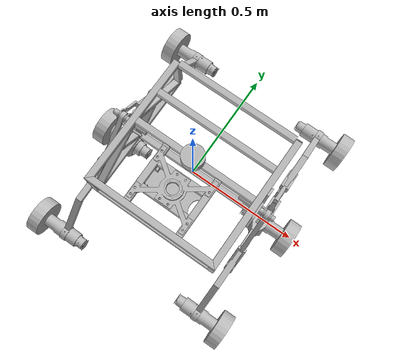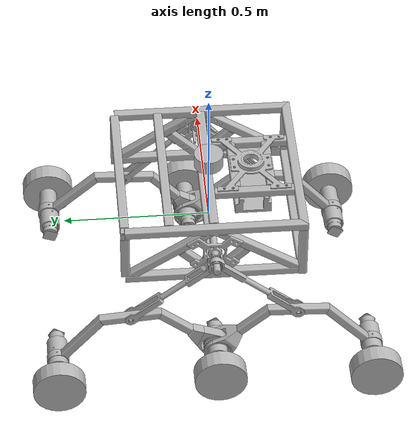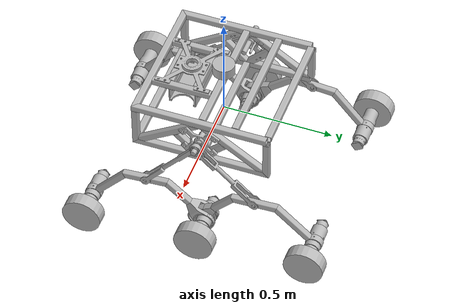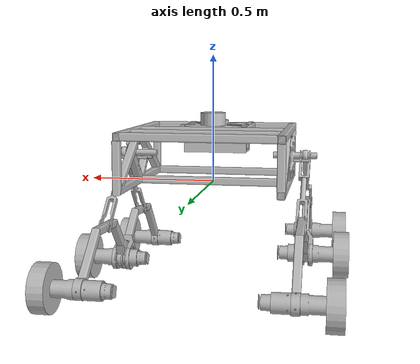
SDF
<sdf version='1.7'>
  <model name='rover'>
    <link name='base_footprint'>
      <inertial>
        <pose>0.00252 -0.038617 0.12348 0 -0 0</pose>
        <mass>9.50689</mass>
        <inertia>
          <ixx>0.351487</ixx>
          <ixy>-0.00291006</ixy>
          <ixz>0.000289974</ixz>
          <iyy>0.573259</iyy>
          <iyz>-0.00666649</iyz>
          <izz>0.804511</izz>
        </inertia>
      </inertial>
      <collision name='base_footprint_fixed_joint_lump__base_link_collision'>
        <pose>0 0 0 0 -0 0</pose>
        <geometry>
          <box>
            <size>0.6 0.5 0.15</size>
          </box>
        </geometry>
      </collision>
      <collision name='base_footprint_fixed_joint_lump__chassis_default_as_machined_collision_1'>
        <pose>-0.295141 0.006002 0.000885 1.56556 -0 -3.14159</pose>
        <geometry>
          <mesh>
            <scale>1 1 1</scale>
            <uri>model://rover_description/meshes/chassis_default_as_machined.dae</uri>
          </mesh>
        </geometry>
      </collision>
      <collision name='base_footprint_fixed_joint_lump__chassis_default_as_machined_collision_2'>
        <pose>-0.295141 0.006002 0.000885 1.56556 -0 -3.14159</pose>
        <geometry>
          <mesh>
            <scale>1 1 1</scale>
            <uri>model://rover_description/meshes/chassis_default_as_machined__2.dae</uri>
          </mesh>
        </geometry>
      </collision>
      <collision name='base_footprint_fixed_joint_lump__chassis_default_as_machined_collision_3'>
        <pose>0.319859 0.005426 0.110883 3.14159 -0.005237 1.5708</pose>
        <geometry>
          <mesh>
            <scale>1 1 1</scale>
            <uri>model://rover_description/meshes/attachment_wheel_to_chassis.dae</uri>
          </mesh>
        </geometry>
      </collision>
      <collision name='base_footprint_fixed_joint_lump__chassis_default_as_machined_collision_4'>
        <pose>-0.295141 0.006002 0.000885 1.56556 -0 -3.14159</pose>
        <geometry>
          <mesh>
            <scale>1 1 1</scale>
            <uri>model://rover_description/meshes/chassis_default_as_machined__3.dae</uri>
          </mesh>
        </geometry>
      </collision>
      <collision name='base_footprint_fixed_joint_lump__chassis_default_as_machined_collision_5'>
        <pose>-0.295141 0.006002 0.000885 1.56556 -0 -3.14159</pose>
        <geometry>
          <mesh>
            <scale>1 1 1</scale>
            <uri>model://rover_description/meshes/chassis_default_as_machined__4.dae</uri>
          </mesh>
        </geometry>
      </collision>
      <collision name='base_footprint_fixed_joint_lump__chassis_default_as_machined_collision_6'>
        <pose>0.004859 -0.306041 0.199253 1.5708 0.005237 -1.5708</pose>
        <geometry>
          <mesh>
            <scale>1 1 1</scale>
            <uri>model://rover_description/meshes/bearing_id_12_od_18.dae</uri>
          </mesh>
        </geometry>
      </collision>
      <collision name='base_footprint_fixed_joint_lump__chassis_default_as_machined_collision_7'>
        <pose>-0.295141 0.006002 0.000885 1.56556 -0 -3.14159</pose>
        <geometry>
          <mesh>
            <scale>1 1 1</scale>
            <uri>model://rover_description/meshes/chassis_default_as_machined__5.dae</uri>
          </mesh>
        </geometry>
      </collision>
      <collision name='base_footprint_fixed_joint_lump__chassis_default_as_machined_collision_8'>
        <pose>-0.295141 0.006002 0.000885 1.56556 -0 -3.14159</pose>
        <geometry>
          <mesh>
            <scale>1 1 1</scale>
            <uri>model://rover_description/meshes/chassis_default_as_machined__6.dae</uri>
          </mesh>
        </geometry>
      </collision>
      <collision name='base_footprint_fixed_joint_lump__chassis_default_as_machined_collision_9'>
        <pose>-0.295141 0.006002 0.000885 1.56556 -0 -3.14159</pose>
        <geometry>
          <mesh>
            <scale>1 1 1</scale>
            <uri>model://rover_description/meshes/chassis_default_as_machined__7.dae</uri>
          </mesh>
        </geometry>
      </collision>
      <collision name='base_footprint_fixed_joint_lump__chassis_default_as_machined_collision_10'>
        <pose>-0.295141 0.006002 0.000885 1.56556 -0 -3.14159</pose>
        <geometry>
          <mesh>
            <scale>1 1 1</scale>
            <uri>model://rover_description/meshes/chassis_default_as_machined__8.dae</uri>
          </mesh>
        </geometry>
      </collision>
      <collision name='base_footprint_fixed_joint_lump__chassis_default_as_machined_collision_11'>
        <pose>-0.320141 0.005426 0.110883 3.14159 -0.005237 1.5708</pose>
        <geometry>
          <mesh>
            <scale>1 1 1</scale>
            <uri>model://rover_description/meshes/attachment_wheel_to_chassis.dae</uri>
          </mesh>
        </geometry>
      </collision>
      <collision name='base_footprint_fixed_joint_lump__chassis_default_as_machined_collision_12'>
        <pose>-0.295141 0.006002 0.000885 1.56556 -0 -3.14159</pose>
        <geometry>
          <mesh>
            <scale>1 1 1</scale>
            <uri>model://rover_description/meshes/chassis_default_as_machined__9.dae</uri>
          </mesh>
        </geometry>
      </collision>
      <collision name='base_footprint_fixed_joint_lump__chassis_default_as_machined_collision_13'>
        <pose>-0.295141 0.006002 0.000885 1.56556 -0 -3.14159</pose>
        <geometry>
          <mesh>
            <scale>1 1 1</scale>
            <uri>model://rover_description/meshes/chassis_default_as_machined__10.dae</uri>
          </mesh>
        </geometry>
      </collision>
      <collision name='base_footprint_fixed_joint_lump__chassis_default_as_machined_collision_14'>
        <pose>-0.295141 0.006002 0.000885 1.56556 -0 -3.14159</pose>
        <geometry>
          <mesh>
            <scale>1 1 1</scale>
            <uri>model://rover_description/meshes/chassis_default_as_machined__11.dae</uri>
          </mesh>
        </geometry>
      </collision>
      <collision name='base_footprint_fixed_joint_lump__chassis_default_as_machined_collision_15'>
        <pose>-0.295141 0.006002 0.000885 1.56556 -0 -3.14159</pose>
        <geometry>
          <mesh>
            <scale>1 1 1</scale>
            <uri>model://rover_description/meshes/chassis_default_as_machined__12.dae</uri>
          </mesh>
        </geometry>
      </collision>
      <collision name='base_footprint_fixed_joint_lump__chassis_default_as_machined_collision_16'>
        <pose>-0.295141 0.006002 0.000885 1.56556 -0 -3.14159</pose>
        <geometry>
          <mesh>
            <scale>1 1 1</scale>
            <uri>model://rover_description/meshes/chassis_default_as_machined__13.dae</uri>
          </mesh>
        </geometry>
      </collision>
      <collision name='base_footprint_fixed_joint_lump__chassis_default_as_machined_collision_17'>
        <pose>-0.295141 0.006002 0.000885 1.56556 -0 -3.14159</pose>
        <geometry>
          <mesh>
            <scale>1 1 1</scale>
            <uri>model://rover_description/meshes/chassis_default_as_machined__14.dae</uri>
          </mesh>
        </geometry>
      </collision>
      <collision name='base_footprint_fixed_joint_lump__chassis_default_as_machined_collision_18'>
        <pose>-0.295141 0.006002 0.000885 1.56556 -0 -3.14159</pose>
        <geometry>
          <mesh>
            <scale>1 1 1</scale>
            <uri>model://rover_description/meshes/chassis_default_as_machined__15.dae</uri>
          </mesh>
        </geometry>
      </collision>
      <collision name='base_footprint_fixed_joint_lump__chassis_default_as_machined_collision_19'>
        <pose>-0.295141 0.006002 0.000885 1.56556 -0 -3.14159</pose>
        <geometry>
          <mesh>
            <scale>1 1 1</scale>
            <uri>model://rover_description/meshes/chassis_default_as_machined__16.dae</uri>
          </mesh>
        </geometry>
      </collision>
      <collision name='base_footprint_fixed_joint_lump__chassis_default_as_machined_collision_20'>
        <pose>-0.295141 0.006002 0.000885 1.56556 -0 -3.14159</pose>
        <geometry>
          <mesh>
            <scale>1 1 1</scale>
            <uri>model://rover_description/meshes/chassis_default_as_machined__17.dae</uri>
          </mesh>
        </geometry>
      </collision>
      <collision name='base_footprint_fixed_joint_lump__chassis_default_as_machined_collision_21'>
        <pose>0.004859 -0.280041 0.19939 1.5708 0.005237 -1.5708</pose>
        <geometry>
          <mesh>
            <scale>1 1 1</scale>
            <uri>model://rover_description/meshes/bearing_id_12_od_18.dae</uri>
          </mesh>
        </geometry>
      </collision>
      <collision name='base_footprint_fixed_joint_lump__chassis_default_as_machined_collision_22'>
        <pose>-0.295141 0.006002 0.000885 1.56556 -0 -3.14159</pose>
        <geometry>
          <mesh>
            <scale>1 1 1</scale>
            <uri>model://rover_description/meshes/chassis_default_as_machined__18.dae</uri>
          </mesh>
        </geometry>
      </collision>
      <collision name='base_footprint_fixed_joint_lump__chassis_default_as_machined_collision_23'>
        <pose>-0.295141 0.006002 0.000885 1.56556 -0 -3.14159</pose>
        <geometry>
          <mesh>
            <scale>1 1 1</scale>
            <uri>model://rover_description/meshes/chassis_default_as_machined__19.dae</uri>
          </mesh>
        </geometry>
      </collision>
      <collision name='base_footprint_fixed_joint_lump__chassis_default_as_machined_collision_24'>
        <pose>-0.295141 0.006002 0.000885 1.56556 -0 -3.14159</pose>
        <geometry>
          <mesh>
            <scale>1 1 1</scale>
            <uri>model://rover_description/meshes/chassis_default_as_machined__20.dae</uri>
          </mesh>
        </geometry>
      </collision>
      <collision name='base_footprint_fixed_joint_lump__chassis_default_as_machined_collision_25'>
        <pose>-0.295141 0.006002 0.000885 1.56556 -0 -3.14159</pose>
        <geometry>
          <mesh>
            <scale>1 1 1</scale>
            <uri>model://rover_description/meshes/chassis_default_as_machined__21.dae</uri>
          </mesh>
        </geometry>
      </collision>
      <collision name='base_footprint_fixed_joint_lump__chassis_default_as_machined_collision_26'>
        <pose>-0.295141 0.006002 0.000885 1.56556 -0 -3.14159</pose>
        <geometry>
          <mesh>
            <scale>1 1 1</scale>
            <uri>model://rover_description/meshes/chassis_default_as_machined__22.dae</uri>
          </mesh>
        </geometry>
      </collision>
      <collision name='base_footprint_fixed_joint_lump__chassis_default_as_machined_collision_27'>
        <pose>0.004859 -0.145122 0.215096 1.56556 -0 -3.14159</pose>
        <geometry>
          <mesh>
            <scale>1 1 1</scale>
            <uri>model://rover_description/meshes/robotic_arm_chassis_base_plate.dae</uri>
          </mesh>
        </geometry>
      </collision>
      <collision name='base_footprint_fixed_joint_lump__chassis_default_as_machined_collision_28'>
        <pose>0.036509 -0.142782 0.105107 1.56556 -0 -3.14159</pose>
        <geometry>
          <mesh>
            <scale>1 1 1</scale>
            <uri>model://rover_description/meshes/gear_system_enclosure.dae</uri>
          </mesh>
        </geometry>
      </collision>
      <collision name='base_footprint_fixed_joint_lump__chassis_default_as_machined_collision_29'>
        <pose>-0.295141 0.006002 0.000885 1.56556 -0 -3.14159</pose>
        <geometry>
          <mesh>
            <scale>1 1 1</scale>
            <uri>model://rover_description/meshes/chassis_default_as_machined__23.dae</uri>
          </mesh>
        </geometry>
      </collision>
      <collision name='base_footprint_fixed_joint_lump__chassis_default_as_machined_collision_30'>
        <pose>-0.295141 0.006002 0.000885 1.56556 -0 -3.14159</pose>
        <geometry>
          <mesh>
            <scale>1 1 1</scale>
            <uri>model://rover_description/meshes/chassis_default_as_machined__24.dae</uri>
          </mesh>
        </geometry>
      </collision>
      <collision name='base_footprint_fixed_joint_lump__chassis_default_as_machined_collision_31'>
        <pose>-0.295141 0.006002 0.000885 1.56556 -0 -3.14159</pose>
        <geometry>
          <mesh>
            <scale>1 1 1</scale>
            <uri>model://rover_description/meshes/chassis_default_as_machined__25.dae</uri>
          </mesh>
        </geometry>
      </collision>
      <collision name='base_footprint_fixed_joint_lump__chassis_default_as_machined_collision_32'>
        <pose>-0.295141 0.006002 0.000885 1.56556 -0 -3.14159</pose>
        <geometry>
          <mesh>
            <scale>1 1 1</scale>
            <uri>model://rover_description/meshes/chassis_default_as_machined__26.dae</uri>
          </mesh>
        </geometry>
      </collision>
      <visual name='base_footprint_fixed_joint_lump__chassis_default_as_machined_visual'>
        <pose>-0.295141 0.006002 0.000885 1.56556 -0 -3.14159</pose>
        <geometry>
          <mesh>
            <scale>1 1 1</scale>
            <uri>model://rover_description/meshes/chassis_default_as_machined.dae</uri>
          </mesh>
        </geometry>
      </visual>
      <visual name='base_footprint_fixed_joint_lump__chassis_default_as_machined_visual_1'>
        <pose>-0.295141 0.006002 0.000885 1.56556 -0 -3.14159</pose>
        <geometry>
          <mesh>
            <scale>1 1 1</scale>
            <uri>model://rover_description/meshes/chassis_default_as_machined__2.dae</uri>
          </mesh>
        </geometry>
      </visual>
      <visual name='base_footprint_fixed_joint_lump__chassis_default_as_machined_visual_2'>
        <pose>0.319859 0.005426 0.110883 3.14159 -0.005237 1.5708</pose>
        <geometry>
          <mesh>
            <scale>1 1 1</scale>
            <uri>model://rover_description/meshes/attachment_wheel_to_chassis.dae</uri>
          </mesh>
        </geometry>
      </visual>
      <visual name='base_footprint_fixed_joint_lump__chassis_default_as_machined_visual_3'>
        <pose>-0.295141 0.006002 0.000885 1.56556 -0 -3.14159</pose>
        <geometry>
          <mesh>
            <scale>1 1 1</scale>
            <uri>model://rover_description/meshes/chassis_default_as_machined__3.dae</uri>
          </mesh>
        </geometry>
      </visual>
      <visual name='base_footprint_fixed_joint_lump__chassis_default_as_machined_visual_4'>
        <pose>-0.295141 0.006002 0.000885 1.56556 -0 -3.14159</pose>
        <geometry>
          <mesh>
            <scale>1 1 1</scale>
            <uri>model://rover_description/meshes/chassis_default_as_machined__4.dae</uri>
          </mesh>
        </geometry>
      </visual>
      <visual name='base_footprint_fixed_joint_lump__chassis_default_as_machined_visual_5'>
        <pose>0.004859 -0.306041 0.199253 1.5708 0.005237 -1.5708</pose>
        <geometry>
          <mesh>
            <scale>1 1 1</scale>
            <uri>model://rover_description/meshes/bearing_id_12_od_18.dae</uri>
          </mesh>
        </geometry>
      </visual>
      <visual name='base_footprint_fixed_joint_lump__chassis_default_as_machined_visual_6'>
        <pose>-0.295141 0.006002 0.000885 1.56556 -0 -3.14159</pose>
        <geometry>
          <mesh>
            <scale>1 1 1</scale>
            <uri>model://rover_description/meshes/chassis_default_as_machined__5.dae</uri>
          </mesh>
        </geometry>
      </visual>
      <visual name='base_footprint_fixed_joint_lump__chassis_default_as_machined_visual_7'>
        <pose>-0.295141 0.006002 0.000885 1.56556 -0 -3.14159</pose>
        <geometry>
          <mesh>
            <scale>1 1 1</scale>
            <uri>model://rover_description/meshes/chassis_default_as_machined__6.dae</uri>
          </mesh>
        </geometry>
      </visual>
      <visual name='base_footprint_fixed_joint_lump__chassis_default_as_machined_visual_8'>
        <pose>-0.295141 0.006002 0.000885 1.56556 -0 -3.14159</pose>
        <geometry>
          <mesh>
            <scale>1 1 1</scale>
            <uri>model://rover_description/meshes/chassis_default_as_machined__7.dae</uri>
          </mesh>
        </geometry>
      </visual>
      <visual name='base_footprint_fixed_joint_lump__chassis_default_as_machined_visual_9'>
        <pose>-0.295141 0.006002 0.000885 1.56556 -0 -3.14159</pose>
        <geometry>
          <mesh>
            <scale>1 1 1</scale>
            <uri>model://rover_description/meshes/chassis_default_as_machined__8.dae</uri>
          </mesh>
        </geometry>
      </visual>
      <visual name='base_footprint_fixed_joint_lump__chassis_default_as_machined_visual_10'>
        <pose>-0.320141 0.005426 0.110883 3.14159 -0.005237 1.5708</pose>
        <geometry>
          <mesh>
            <scale>1 1 1</scale>
            <uri>model://rover_description/meshes/attachment_wheel_to_chassis.dae</uri>
          </mesh>
        </geometry>
      </visual>
      <visual name='base_footprint_fixed_joint_lump__chassis_default_as_machined_visual_11'>
        <pose>-0.295141 0.006002 0.000885 1.56556 -0 -3.14159</pose>
        <geometry>
          <mesh>
            <scale>1 1 1</scale>
            <uri>model://rover_description/meshes/chassis_default_as_machined__9.dae</uri>
          </mesh>
        </geometry>
      </visual>
      <visual name='base_footprint_fixed_joint_lump__chassis_default_as_machined_visual_12'>
        <pose>-0.295141 0.006002 0.000885 1.56556 -0 -3.14159</pose>
        <geometry>
          <mesh>
            <scale>1 1 1</scale>
            <uri>model://rover_description/meshes/chassis_default_as_machined__10.dae</uri>
          </mesh>
        </geometry>
      </visual>
      <visual name='base_footprint_fixed_joint_lump__chassis_default_as_machined_visual_13'>
        <pose>-0.295141 0.006002 0.000885 1.56556 -0 -3.14159</pose>
        <geometry>
          <mesh>
            <scale>1 1 1</scale>
            <uri>model://rover_description/meshes/chassis_default_as_machined__11.dae</uri>
          </mesh>
        </geometry>
      </visual>
      <visual name='base_footprint_fixed_joint_lump__chassis_default_as_machined_visual_14'>
        <pose>-0.295141 0.006002 0.000885 1.56556 -0 -3.14159</pose>
        <geometry>
          <mesh>
            <scale>1 1 1</scale>
            <uri>model://rover_description/meshes/chassis_default_as_machined__12.dae</uri>
          </mesh>
        </geometry>
      </visual>
      <visual name='base_footprint_fixed_joint_lump__chassis_default_as_machined_visual_15'>
        <pose>-0.295141 0.006002 0.000885 1.56556 -0 -3.14159</pose>
        <geometry>
          <mesh>
            <scale>1 1 1</scale>
            <uri>model://rover_description/meshes/chassis_default_as_machined__13.dae</uri>
          </mesh>
        </geometry>
      </visual>
      <visual name='base_footprint_fixed_joint_lump__chassis_default_as_machined_visual_16'>
        <pose>-0.295141 0.006002 0.000885 1.56556 -0 -3.14159</pose>
        <geometry>
          <mesh>
            <scale>1 1 1</scale>
            <uri>model://rover_description/meshes/chassis_default_as_machined__14.dae</uri>
          </mesh>
        </geometry>
      </visual>
      <visual name='base_footprint_fixed_joint_lump__chassis_default_as_machined_visual_17'>
        <pose>-0.295141 0.006002 0.000885 1.56556 -0 -3.14159</pose>
        <geometry>
          <mesh>
            <scale>1 1 1</scale>
            <uri>model://rover_description/meshes/chassis_default_as_machined__15.dae</uri>
          </mesh>
        </geometry>
      </visual>
      <visual name='base_footprint_fixed_joint_lump__chassis_default_as_machined_visual_18'>
        <pose>-0.295141 0.006002 0.000885 1.56556 -0 -3.14159</pose>
        <geometry>
          <mesh>
            <scale>1 1 1</scale>
            <uri>model://rover_description/meshes/chassis_default_as_machined__16.dae</uri>
          </mesh>
        </geometry>
      </visual>
      <visual name='base_footprint_fixed_joint_lump__chassis_default_as_machined_visual_19'>
        <pose>-0.295141 0.006002 0.000885 1.56556 -0 -3.14159</pose>
        <geometry>
          <mesh>
            <scale>1 1 1</scale>
            <uri>model://rover_description/meshes/chassis_default_as_machined__17.dae</uri>
          </mesh>
        </geometry>
      </visual>
      <visual name='base_footprint_fixed_joint_lump__chassis_default_as_machined_visual_20'>
        <pose>0.004859 -0.280041 0.19939 1.5708 0.005237 -1.5708</pose>
        <geometry>
          <mesh>
            <scale>1 1 1</scale>
            <uri>model://rover_description/meshes/bearing_id_12_od_18.dae</uri>
          </mesh>
        </geometry>
      </visual>
      <visual name='base_footprint_fixed_joint_lump__chassis_default_as_machined_visual_21'>
        <pose>-0.295141 0.006002 0.000885 1.56556 -0 -3.14159</pose>
        <geometry>
          <mesh>
            <scale>1 1 1</scale>
            <uri>model://rover_description/meshes/chassis_default_as_machined__18.dae</uri>
          </mesh>
        </geometry>
      </visual>
      <visual name='base_footprint_fixed_joint_lump__chassis_default_as_machined_visual_22'>
        <pose>-0.295141 0.006002 0.000885 1.56556 -0 -3.14159</pose>
        <geometry>
          <mesh>
            <scale>1 1 1</scale>
            <uri>model://rover_description/meshes/chassis_default_as_machined__19.dae</uri>
          </mesh>
        </geometry>
      </visual>
      <visual name='base_footprint_fixed_joint_lump__chassis_default_as_machined_visual_23'>
        <pose>-0.295141 0.006002 0.000885 1.56556 -0 -3.14159</pose>
        <geometry>
          <mesh>
            <scale>1 1 1</scale>
            <uri>model://rover_description/meshes/chassis_default_as_machined__20.dae</uri>
          </mesh>
        </geometry>
      </visual>
      <visual name='base_footprint_fixed_joint_lump__chassis_default_as_machined_visual_24'>
        <pose>-0.295141 0.006002 0.000885 1.56556 -0 -3.14159</pose>
        <geometry>
          <mesh>
            <scale>1 1 1</scale>
            <uri>model://rover_description/meshes/chassis_default_as_machined__21.dae</uri>
          </mesh>
        </geometry>
      </visual>
      <visual name='base_footprint_fixed_joint_lump__chassis_default_as_machined_visual_25'>
        <pose>-0.295141 0.006002 0.000885 1.56556 -0 -3.14159</pose>
        <geometry>
          <mesh>
            <scale>1 1 1</scale>
            <uri>model://rover_description/meshes/chassis_default_as_machined__22.dae</uri>
          </mesh>
        </geometry>
      </visual>
      <visual name='base_footprint_fixed_joint_lump__chassis_default_as_machined_visual_26'>
        <pose>0.004859 -0.145122 0.215096 1.56556 -0 -3.14159</pose>
        <geometry>
          <mesh>
            <scale>1 1 1</scale>
            <uri>model://rover_description/meshes/robotic_arm_chassis_base_plate.dae</uri>
          </mesh>
        </geometry>
      </visual>
      <visual name='base_footprint_fixed_joint_lump__chassis_default_as_machined_visual_27'>
        <pose>0.036509 -0.142782 0.105107 1.56556 -0 -3.14159</pose>
        <geometry>
          <mesh>
            <scale>1 1 1</scale>
            <uri>model://rover_description/meshes/gear_system_enclosure.dae</uri>
          </mesh>
        </geometry>
      </visual>
      <visual name='base_footprint_fixed_joint_lump__chassis_default_as_machined_visual_28'>
        <pose>-0.295141 0.006002 0.000885 1.56556 -0 -3.14159</pose>
        <geometry>
          <mesh>
            <scale>1 1 1</scale>
            <uri>model://rover_description/meshes/chassis_default_as_machined__23.dae</uri>
          </mesh>
        </geometry>
      </visual>
      <visual name='base_footprint_fixed_joint_lump__chassis_default_as_machined_visual_29'>
        <pose>-0.295141 0.006002 0.000885 1.56556 -0 -3.14159</pose>
        <geometry>
          <mesh>
            <scale>1 1 1</scale>
            <uri>model://rover_description/meshes/chassis_default_as_machined__24.dae</uri>
          </mesh>
        </geometry>
      </visual>
      <visual name='base_footprint_fixed_joint_lump__chassis_default_as_machined_visual_30'>
        <pose>-0.295141 0.006002 0.000885 1.56556 -0 -3.14159</pose>
        <geometry>
          <mesh>
            <scale>1 1 1</scale>
            <uri>model://rover_description/meshes/chassis_default_as_machined__25.dae</uri>
          </mesh>
        </geometry>
      </visual>
      <visual name='base_footprint_fixed_joint_lump__chassis_default_as_machined_visual_31'>
        <pose>-0.295141 0.006002 0.000885 1.56556 -0 -3.14159</pose>
        <geometry>
          <mesh>
            <scale>1 1 1</scale>
            <uri>model://rover_description/meshes/chassis_default_as_machined__26.dae</uri>
          </mesh>
        </geometry>
      </visual>
    </link>
    <joint name='BL_Rod' type='revolute'>
      <pose relative_to='base_footprint'>0.349619 0.005426 0.110883 -1.5708 -1.56232 -1.5708</pose>
      <parent>base_footprint</parent>
      <child>shaft_10_torsion_mechanism_3</child>
      <axis>
        <xyz>0 0 1</xyz>
        <limit>
          <lower>-0.439569</lower>
          <upper>1.91663</upper>
          <effort>10</effort>
          <velocity>10</velocity>
        </limit>
        <dynamics>
          <spring_reference>0</spring_reference>
          <spring_stiffness>0</spring_stiffness>
        </dynamics>
      </axis>
    </joint>
    <link name='shaft_10_torsion_mechanism_3'>
      <pose relative_to='BL_Rod'>0 0 0 0 -0 0</pose>
      <inertial>
        <pose>-0.127916 -0.134285 0.012377 0 -0 0</pose>
        <mass>0.386504</mass>
        <inertia>
          <ixx>0.00249876</ixx>
          <ixy>-0.00223606</ixy>
          <ixz>0.000108577</ixz>
          <iyy>0.00228032</iyy>
          <iyz>0.000114122</iyz>
          <izz>0.00451162</izz>
        </inertia>
      </inertial>
      <collision name='shaft_10_torsion_mechanism_3_collision'>
        <pose>-0.01938 -0.020209 -0.08477 1.5708 0 -1.67145</pose>
        <geometry>
          <mesh>
            <scale>1 1 1</scale>
            <uri>model://rover_description/meshes/shaft_10_torsion_mechanism.dae</uri>
          </mesh>
        </geometry>
      </collision>
      <collision name='shaft_10_torsion_mechanism_3_collision_1'>
        <pose>-0.109806 -0.02035 -0.631123 1.5708 1.5708 0</pose>
        <geometry>
          <mesh>
            <scale>1 1 1</scale>
            <uri>model://rover_description/meshes/chassis_to_trapezoid_both_side_double_eye_1.dae</uri>
          </mesh>
        </geometry>
      </collision>
      <visual name='shaft_10_torsion_mechanism_3_visual'>
        <pose>-0.01938 -0.020209 -0.08477 1.5708 0 -1.67145</pose>
        <geometry>
          <mesh>
            <scale>1 1 1</scale>
            <uri>model://rover_description/meshes/shaft_10_torsion_mechanism.dae</uri>
          </mesh>
        </geometry>
      </visual>
      <visual name='shaft_10_torsion_mechanism_3_visual_1'>
        <pose>-0.109806 -0.02035 -0.631123 1.5708 1.5708 0</pose>
        <geometry>
          <mesh>
            <scale>1 1 1</scale>
            <uri>model://rover_description/meshes/chassis_to_trapezoid_both_side_double_eye_1.dae</uri>
          </mesh>
        </geometry>
      </visual>
    </link>
    <joint name='BL_Trap' type='revolute'>
      <pose relative_to='shaft_10_torsion_mechanism_3'>-0.254918 -0.267628 0.03 0 0 -1.52526</pose>
      <parent>shaft_10_torsion_mechanism_3</parent>
      <child>trapezoid_single_eye_default_as_machined_2</child>
      <axis>
        <xyz>0 0 1</xyz>
        <limit>
          <lower>-0.569131</lower>
          <upper>2.2234</upper>
          <effort>10</effort>
          <velocity>10</velocity>
        </limit>
        <dynamics>
          <spring_reference>0</spring_reference>
          <spring_stiffness>0</spring_stiffness>
        </dynamics>
      </axis>
    </joint>
    <link name='trapezoid_single_eye_default_as_machined_2'>
      <velocity_decay>
        <linear>0.1</linear>
        <angular>0.1</angular>
      </velocity_decay>
      <pose relative_to='BL_Trap'>0 0 0 0 -0 0</pose>
      <inertial>
        <pose>0.148357 -0.145548 -0.017429 0 -0 0</pose>
        <mass>2.75976</mass>
        <inertia>
          <ixx>0.0141228</ixx>
          <ixy>0.0133809</ixy>
          <ixz>0.000792451</ixz>
          <iyy>0.114971</iyy>
          <iyz>-0.000167131</iyz>
          <izz>0.115717</izz>
        </inertia>
      </inertial>
      <collision name='trapezoid_single_eye_default_as_machined_2_collision'>
        <pose>0 0 -0.015 1.5708 -0 0</pose>
        <geometry>
          <mesh>
            <scale>1 1 1</scale>
            <uri>model://rover_description/meshes/trapezoid_single_eye_default_as_machined__2.dae</uri>
          </mesh>
        </geometry>
      </collision>
      <collision name='trapezoid_single_eye_default_as_machined_2_collision_1'>
        <pose>0.266536 -0.170493 0.045236 2.83659 1.5708 0</pose>
        <geometry>
          <mesh>
            <scale>1 1 1</scale>
            <uri>model://rover_description/meshes/motor_160kg_cm_ig52__3.dae</uri>
          </mesh>
        </geometry>
      </collision>
      <collision name='trapezoid_single_eye_default_as_machined_2_collision_2'>
        <pose>0 0 -0.015 1.5708 -0 0</pose>
        <geometry>
          <mesh>
            <scale>1 1 1</scale>
            <uri>model://rover_description/meshes/trapezoid_single_eye_default_as_machined__6.dae</uri>
          </mesh>
        </geometry>
      </collision>
      <collision name='trapezoid_single_eye_default_as_machined_2_collision_3'>
        <pose>0 0 -0.015 1.5708 -0 0</pose>
        <geometry>
          <mesh>
            <scale>1 1 1</scale>
            <uri>model://rover_description/meshes/trapezoid_single_eye_default_as_machined__4.dae</uri>
          </mesh>
        </geometry>
      </collision>
      <collision name='trapezoid_single_eye_default_as_machined_2_collision_4'>
        <pose>0 0 -0.015 1.5708 -0 0</pose>
        <geometry>
          <mesh>
            <scale>1 1 1</scale>
            <uri>model://rover_description/meshes/trapezoid_single_eye_default_as_machined__5.dae</uri>
          </mesh>
        </geometry>
      </collision>
      <collision name='trapezoid_single_eye_default_as_machined_2_collision_5'>
        <pose>0 0 -0.015 1.5708 -0 0</pose>
        <geometry>
          <mesh>
            <scale>1 1 1</scale>
            <uri>model://rover_description/meshes/trapezoid_single_eye_default_as_machined__7.dae</uri>
          </mesh>
        </geometry>
      </collision>
      <collision name='trapezoid_single_eye_default_as_machined_2_collision_6'>
        <pose>0 0 -0.015 1.5708 -0 0</pose>
        <geometry>
          <mesh>
            <scale>1 1 1</scale>
            <uri>model://rover_description/meshes/trapezoid_single_eye_default_as_machined__3.dae</uri>
          </mesh>
        </geometry>
      </collision>
      <collision name='trapezoid_single_eye_default_as_machined_2_collision_7'>
        <pose>0.266536 -0.170493 0.046736 2.83659 1.5708 0</pose>
        <geometry>
          <mesh>
            <scale>1 1 1</scale>
            <uri>model://rover_description/meshes/motor_160kg_cm_ig52__4.dae</uri>
          </mesh>
        </geometry>
      </collision>
      <collision name='trapezoid_single_eye_default_as_machined_2_collision_8'>
        <pose>0.266536 -0.170493 -0.01354 -0.304999 1.5708 0</pose>
        <geometry>
          <mesh>
            <scale>1 1 1</scale>
            <uri>model://rover_description/meshes/16_kg_motor_housing__2.dae</uri>
          </mesh>
        </geometry>
      </collision>
      <visual name='trapezoid_single_eye_default_as_machined_2_visual'>
        <pose>0 0 -0.015 1.5708 -0 0</pose>
        <geometry>
          <mesh>
            <scale>1 1 1</scale>
            <uri>model://rover_description/meshes/trapezoid_single_eye_default_as_machined__2.dae</uri>
          </mesh>
        </geometry>
      </visual>
      <visual name='trapezoid_single_eye_default_as_machined_2_visual_1'>
        <pose>0.266536 -0.170493 0.045236 2.83659 1.5708 0</pose>
        <geometry>
          <mesh>
            <scale>1 1 1</scale>
            <uri>model://rover_description/meshes/motor_160kg_cm_ig52__3.dae</uri>
          </mesh>
        </geometry>
      </visual>
      <visual name='trapezoid_single_eye_default_as_machined_2_visual_2'>
        <pose>0 0 -0.015 1.5708 -0 0</pose>
        <geometry>
          <mesh>
            <scale>1 1 1</scale>
            <uri>model://rover_description/meshes/trapezoid_single_eye_default_as_machined__6.dae</uri>
          </mesh>
        </geometry>
      </visual>
      <visual name='trapezoid_single_eye_default_as_machined_2_visual_3'>
        <pose>0 0 -0.015 1.5708 -0 0</pose>
        <geometry>
          <mesh>
            <scale>1 1 1</scale>
            <uri>model://rover_description/meshes/trapezoid_single_eye_default_as_machined__4.dae</uri>
          </mesh>
        </geometry>
      </visual>
      <visual name='trapezoid_single_eye_default_as_machined_2_visual_4'>
        <pose>0 0 -0.015 1.5708 -0 0</pose>
        <geometry>
          <mesh>
            <scale>1 1 1</scale>
            <uri>model://rover_description/meshes/trapezoid_single_eye_default_as_machined__5.dae</uri>
          </mesh>
        </geometry>
      </visual>
      <visual name='trapezoid_single_eye_default_as_machined_2_visual_5'>
        <pose>0 0 -0.015 1.5708 -0 0</pose>
        <geometry>
          <mesh>
            <scale>1 1 1</scale>
            <uri>model://rover_description/meshes/trapezoid_single_eye_default_as_machined__7.dae</uri>
          </mesh>
        </geometry>
      </visual>
      <visual name='trapezoid_single_eye_default_as_machined_2_visual_6'>
        <pose>0 0 -0.015 1.5708 -0 0</pose>
        <geometry>
          <mesh>
            <scale>1 1 1</scale>
            <uri>model://rover_description/meshes/trapezoid_single_eye_default_as_machined__3.dae</uri>
          </mesh>
        </geometry>
      </visual>
      <visual name='trapezoid_single_eye_default_as_machined_2_visual_7'>
        <pose>0.266536 -0.170493 0.046736 2.83659 1.5708 0</pose>
        <geometry>
          <mesh>
            <scale>1 1 1</scale>
            <uri>model://rover_description/meshes/motor_160kg_cm_ig52__4.dae</uri>
          </mesh>
        </geometry>
      </visual>
      <visual name='trapezoid_single_eye_default_as_machined_2_visual_8'>
        <pose>0.266536 -0.170493 -0.01354 -0.304999 1.5708 0</pose>
        <geometry>
          <mesh>
            <scale>1 1 1</scale>
            <uri>model://rover_description/meshes/16_kg_motor_housing__2.dae</uri>
          </mesh>
        </geometry>
      </visual>
    </link>
    <joint name='BL_wheel' type='revolute'>
      <pose relative_to='trapezoid_single_eye_default_as_machined_2'>0.266536 -0.170493 0.112252 -3.14159 -0 -2.83659</pose>
      <parent>trapezoid_single_eye_default_as_machined_2</parent>
      <child>sheet_metal_motor_tyre_2_2</child>
      <axis>
        <xyz>0 0 -1</xyz>
        <limit>
          <effort>10</effort>
          <velocity>10</velocity>
          <lower>-1e+16</lower>
          <upper>1e+16</upper>
        </limit>
        <dynamics>
          <spring_reference>0</spring_reference>
          <spring_stiffness>0</spring_stiffness>
        </dynamics>
      </axis>
    </joint>
    <link name='sheet_metal_motor_tyre_2_2'>
      <pose relative_to='BL_wheel'>0 0 0 0 -0 0</pose>
      <inertial>
        <pose>0.000463 5e-06 0.026652 0 -0 0</pose>
        <mass>5.26097</mass>
        <inertia>
          <ixx>0.0324874</ixx>
          <ixy>1.7127e-08</ixy>
          <ixz>-2.79212e-06</ixz>
          <iyy>0.0326651</iyy>
          <iyz>-2.11648e-06</iyz>
          <izz>0.0517133</izz>
        </inertia>
      </inertial>
      <collision name='sheet_metal_motor_tyre_2_2_collision'>
        <pose>0 0 0 0 -0 0</pose>
        <geometry>
          <cylinder>
            <length>0.06</length>
            <radius>0.09</radius>
          </cylinder>
        </geometry>
        <surface>
          <contact>
            <ode>
              <kp>1e+07</kp>
              <kd>1</kd>
            </ode>
          </contact>
          <friction>
            <ode>
              <fdir1>1 0 0</fdir1>
              <mu>1.5</mu>
              <mu2>0.2</mu2>
            </ode>
             <bullet>
    <friction>1.5</friction>
    <friction2>0.2</friction2>
    <fdir1>1 0 0</fdir1>
    <rolling_friction>0.1</rolling_friction>
  </bullet>
          </friction>
        </surface>
      </collision>
      <visual name='sheet_metal_motor_tyre_2_2_visual'>
        <pose>0 0 0 0 -0 0</pose>
        <geometry>
          <cylinder>
            <length>0.06</length>
            <radius>0.09</radius>
          </cylinder>
        </geometry>
      </visual>
    </link>
    <joint name='BR_Rod' type='revolute'>
      <pose relative_to='base_footprint'>-0.380381 0.005426 0.110883 -1.5708 0.903014 -1.5708</pose>
      <parent>base_footprint</parent>
      <child>shaft_10_torsion_mechanism</child>
      <axis>
        <xyz>0 0 1</xyz>
        <limit>
          <lower>-0.461445</lower>
          <upper>1.80748</upper>
          <effort>10</effort>
          <velocity>10</velocity>
        </limit>
        <dynamics>
          <spring_reference>0</spring_reference>
          <spring_stiffness>0</spring_stiffness>
        </dynamics>
      </axis>
    </joint>
    <link name='shaft_10_torsion_mechanism'>
      <pose relative_to='BR_Rod'>0 0 0 0 -0 0</pose>
      <inertial>
        <pose>-0 0.185459 0.017685 0 -0 0</pose>
        <mass>0.386504</mass>
        <inertia>
          <ixx>0.00462913</ixx>
          <ixy>-4.08e-10</ixy>
          <ixz>-2.3e-11</ixz>
          <iyy>0.000151671</iyy>
          <iyz>0.000165482</iyz>
          <izz>0.00451162</izz>
        </inertia>
      </inertial>
      <collision name='shaft_10_torsion_mechanism_collision'>
        <pose>0 0.004802 0.03525 3.14159 -0 0</pose>
        <geometry>
          <mesh>
            <scale>1 1 1</scale>
            <uri>model://rover_description/meshes/chassis_to_trapezoid_both_side_double_eye.dae</uri>
          </mesh>
        </geometry>
      </collision>
      <collision name='shaft_10_torsion_mechanism_collision_1'>
        <pose>0 0.028 -0.00475 1.5708 -0 -0.919596</pose>
        <geometry>
          <mesh>
            <scale>1 1 1</scale>
            <uri>model://rover_description/meshes/shaft_10_torsion_mechanism.dae</uri>
          </mesh>
        </geometry>
      </collision>
      <visual name='shaft_10_torsion_mechanism_visual'>
        <pose>0 0.004802 0.03525 3.14159 -0 0</pose>
        <geometry>
          <mesh>
            <scale>1 1 1</scale>
            <uri>model://rover_description/meshes/chassis_to_trapezoid_both_side_double_eye.dae</uri>
          </mesh>
        </geometry>
      </visual>
      <visual name='shaft_10_torsion_mechanism_visual_1'>
        <pose>0 0.028 -0.00475 1.5708 -0 -0.919596</pose>
        <geometry>
          <mesh>
            <scale>1 1 1</scale>
            <uri>model://rover_description/meshes/shaft_10_torsion_mechanism.dae</uri>
          </mesh>
        </geometry>
      </visual>
    </link>
    <joint name='BR_Trap' type='revolute'>
      <pose relative_to='shaft_10_torsion_mechanism'>0 0.369605 0 3.14159 -0 2.15666</pose>
      <parent>shaft_10_torsion_mechanism</parent>
      <child>trapezoid_single_eye_default_as_machined</child>
      <axis>
        <xyz>0 0 1</xyz>
        <limit>
          <lower>-2.38119</lower>
          <upper>0.411332</upper>
          <effort>10</effort>
          <velocity>10</velocity>
        </limit>
        <dynamics>
          <spring_reference>0</spring_reference>
          <spring_stiffness>0</spring_stiffness>
        </dynamics>
      </axis>
    </joint>
    <link name='trapezoid_single_eye_default_as_machined'>
      <velocity_decay>
        <linear>0.1</linear>
        <angular>0.1</angular>
      </velocity_decay>
      <pose relative_to='BR_Trap'>0 0 0 0 -0 0</pose>
      <inertial>
        <pose>0.1495 0.142776 -0.016789 0 -0 0</pose>
        <mass>2.75976</mass>
        <inertia>
          <ixx>0.013759</ixx>
          <ixy>-0.0125511</ixy>
          <ixz>0.00058621</ixz>
          <iyy>0.115725</iyy>
          <iyz>0.000116192</iyz>
          <izz>0.116094</izz>
        </inertia>
      </inertial>
      <collision name='trapezoid_single_eye_default_as_machined_collision'>
        <pose>0.268274 0.166273 -0.012195 -1.87277 1.5708 0</pose>
        <geometry>
          <mesh>
            <scale>1 1 1</scale>
            <uri>model://rover_description/meshes/16_kg_motor_housing__2.dae</uri>
          </mesh>
        </geometry>
      </collision>
      <collision name='trapezoid_single_eye_default_as_machined_collision_1'>
        <pose>0 0 -0.015 -1.5708 0 0</pose>
        <geometry>
          <mesh>
            <scale>1 1 1</scale>
            <uri>model://rover_description/meshes/trapezoid_single_eye_default_as_machined__2.dae</uri>
          </mesh>
        </geometry>
      </collision>
      <collision name='trapezoid_single_eye_default_as_machined_collision_2'>
        <pose>0 0 -0.015 -1.5708 0 0</pose>
        <geometry>
          <mesh>
            <scale>1 1 1</scale>
            <uri>model://rover_description/meshes/trapezoid_single_eye_default_as_machined__3.dae</uri>
          </mesh>
        </geometry>
      </collision>
      <collision name='trapezoid_single_eye_default_as_machined_collision_3'>
        <pose>0 0 -0.015 -1.5708 0 0</pose>
        <geometry>
          <mesh>
            <scale>1 1 1</scale>
            <uri>model://rover_description/meshes/trapezoid_single_eye_default_as_machined__4.dae</uri>
          </mesh>
        </geometry>
      </collision>
      <collision name='trapezoid_single_eye_default_as_machined_collision_4'>
        <pose>0 0 -0.015 -1.5708 0 0</pose>
        <geometry>
          <mesh>
            <scale>1 1 1</scale>
            <uri>model://rover_description/meshes/trapezoid_single_eye_default_as_machined__5.dae</uri>
          </mesh>
        </geometry>
      </collision>
      <collision name='trapezoid_single_eye_default_as_machined_collision_5'>
        <pose>0 0 -0.015 -1.5708 0 0</pose>
        <geometry>
          <mesh>
            <scale>1 1 1</scale>
            <uri>model://rover_description/meshes/trapezoid_single_eye_default_as_machined__6.dae</uri>
          </mesh>
        </geometry>
      </collision>
      <collision name='trapezoid_single_eye_default_as_machined_collision_6'>
        <pose>0 0 -0.015 -1.5708 0 0</pose>
        <geometry>
          <mesh>
            <scale>1 1 1</scale>
            <uri>model://rover_description/meshes/trapezoid_single_eye_default_as_machined__7.dae</uri>
          </mesh>
        </geometry>
      </collision>
      <collision name='trapezoid_single_eye_default_as_machined_collision_7'>
        <pose>0.268274 0.166273 0.046081 0.67448 1.5708 0</pose>
        <geometry>
          <mesh>
            <scale>1 1 1</scale>
            <uri>model://rover_description/meshes/motor_160kg_cm_ig52__3.dae</uri>
          </mesh>
        </geometry>
      </collision>
      <collision name='trapezoid_single_eye_default_as_machined_collision_8'>
        <pose>0.268274 0.166273 0.046081 0.67448 1.5708 0</pose>
        <geometry>
          <mesh>
            <scale>1 1 1</scale>
            <uri>model://rover_description/meshes/motor_160kg_cm_ig52__4.dae</uri>
          </mesh>
        </geometry>
      </collision>
      <visual name='trapezoid_single_eye_default_as_machined_visual'>
        <pose>0.268274 0.166273 -0.012195 -1.87277 1.5708 0</pose>
        <geometry>
          <mesh>
            <scale>1 1 1</scale>
            <uri>model://rover_description/meshes/16_kg_motor_housing__2.dae</uri>
          </mesh>
        </geometry>
      </visual>
      <visual name='trapezoid_single_eye_default_as_machined_visual_1'>
        <pose>0 0 -0.015 -1.5708 0 0</pose>
        <geometry>
          <mesh>
            <scale>1 1 1</scale>
            <uri>model://rover_description/meshes/trapezoid_single_eye_default_as_machined__2.dae</uri>
          </mesh>
        </geometry>
      </visual>
      <visual name='trapezoid_single_eye_default_as_machined_visual_2'>
        <pose>0 0 -0.015 -1.5708 0 0</pose>
        <geometry>
          <mesh>
            <scale>1 1 1</scale>
            <uri>model://rover_description/meshes/trapezoid_single_eye_default_as_machined__3.dae</uri>
          </mesh>
        </geometry>
      </visual>
      <visual name='trapezoid_single_eye_default_as_machined_visual_3'>
        <pose>0 0 -0.015 -1.5708 0 0</pose>
        <geometry>
          <mesh>
            <scale>1 1 1</scale>
            <uri>model://rover_description/meshes/trapezoid_single_eye_default_as_machined__4.dae</uri>
          </mesh>
        </geometry>
      </visual>
      <visual name='trapezoid_single_eye_default_as_machined_visual_4'>
        <pose>0 0 -0.015 -1.5708 0 0</pose>
        <geometry>
          <mesh>
            <scale>1 1 1</scale>
            <uri>model://rover_description/meshes/trapezoid_single_eye_default_as_machined__5.dae</uri>
          </mesh>
        </geometry>
      </visual>
      <visual name='trapezoid_single_eye_default_as_machined_visual_5'>
        <pose>0 0 -0.015 -1.5708 0 0</pose>
        <geometry>
          <mesh>
            <scale>1 1 1</scale>
            <uri>model://rover_description/meshes/trapezoid_single_eye_default_as_machined__6.dae</uri>
          </mesh>
        </geometry>
      </visual>
      <visual name='trapezoid_single_eye_default_as_machined_visual_6'>
        <pose>0 0 -0.015 -1.5708 0 0</pose>
        <geometry>
          <mesh>
            <scale>1 1 1</scale>
            <uri>model://rover_description/meshes/trapezoid_single_eye_default_as_machined__7.dae</uri>
          </mesh>
        </geometry>
      </visual>
      <visual name='trapezoid_single_eye_default_as_machined_visual_7'>
        <pose>0.268274 0.166273 0.046081 0.67448 1.5708 0</pose>
        <geometry>
          <mesh>
            <scale>1 1 1</scale>
            <uri>model://rover_description/meshes/motor_160kg_cm_ig52__3.dae</uri>
          </mesh>
        </geometry>
      </visual>
      <visual name='trapezoid_single_eye_default_as_machined_visual_8'>
        <pose>0.268274 0.166273 0.046081 0.67448 1.5708 0</pose>
        <geometry>
          <mesh>
            <scale>1 1 1</scale>
            <uri>model://rover_description/meshes/motor_160kg_cm_ig52__4.dae</uri>
          </mesh>
        </geometry>
      </visual>
    </link>
    <joint name='BR_wheel' type='revolute'>
      <pose relative_to='trapezoid_single_eye_default_as_machined'>0.268274 0.166273 0.113097 -3.14159 -0 -0.674482</pose>
      <parent>trapezoid_single_eye_default_as_machined</parent>
      <child>sheet_metal_motor_tyre_fr_3</child>
      <axis>
        <xyz>0 0 1</xyz>
        <limit>
          <effort>10</effort>
          <velocity>10</velocity>
          <lower>-1e+16</lower>
          <upper>1e+16</upper>
        </limit>
        <dynamics>
          <spring_reference>0</spring_reference>
          <spring_stiffness>0</spring_stiffness>
        </dynamics>
      </axis>
    </joint>
    <link name='sheet_metal_motor_tyre_fr_3'>
      <pose relative_to='BR_wheel'>0 0 0 0 -0 0</pose>
      <inertial>
        <pose>0.000463 5e-06 0.026652 0 -0 0</pose>
        <mass>5.26097</mass>
        <inertia>
          <ixx>0.0324874</ixx>
          <ixy>1.7127e-08</ixy>
          <ixz>-2.79212e-06</ixz>
          <iyy>0.0326651</iyy>
          <iyz>-2.11648e-06</iyz>
          <izz>0.0517133</izz>
        </inertia>
      </inertial>
      <collision name='sheet_metal_motor_tyre_fr_3_collision'>
        <pose>0 0 0 0 -0 0</pose>
        <geometry>
          <cylinder>
            <length>0.06</length>
            <radius>0.09</radius>
          </cylinder>
        </geometry>
        <surface>
          <contact>
            <ode>
              <kp>1e+07</kp>
              <kd>1</kd>
            </ode>
          </contact>
          <friction>
            <ode>
              <fdir1>1 0 0</fdir1>
              <mu>1.5</mu>
              <mu2>0.2</mu2>
            </ode>
             <bullet>
    <friction>1.5</friction>
    <friction2>0.2</friction2>
    <fdir1>1 0 0</fdir1>
    <rolling_friction>0.1</rolling_friction>
  </bullet>
          </friction>
        </surface>
      </collision>
      <visual name='sheet_metal_motor_tyre_fr_3_visual'>
        <pose>0 0 0 0 -0 0</pose>
        <geometry>
          <cylinder>
            <length>0.06</length>
            <radius>0.09</radius>
          </cylinder>
        </geometry>
      </visual>
    </link>
    <joint name='FL_Rod' type='revolute'>
      <pose relative_to='base_footprint'>0.364859 0.005426 0.110883 -1.5708 0.693807 1.5708</pose>
      <parent>base_footprint</parent>
      <child>shaft_10_torsion_mechanism_2</child>
      <axis>
        <xyz>0 0 1</xyz>
        <limit>
          <lower>-0.349978</lower>
          <upper>2.05858</upper>
          <effort>10</effort>
          <velocity>10</velocity>
        </limit>
        <dynamics>
          <spring_reference>0</spring_reference>
          <spring_stiffness>0</spring_stiffness>
        </dynamics>
      </axis>
    </joint>
    <link name='shaft_10_torsion_mechanism_2'>
      <pose relative_to='FL_Rod'>0 0 0 0 -0 0</pose>
      <inertial>
        <pose>0 0.171668 0.003188 0 -0 0</pose>
        <mass>0.4139</mass>
        <inertia>
          <ixx>0.00559507</ixx>
          <ixy>-3.36e-10</ixy>
          <ixz>-5.7e-11</ixz>
          <iyy>0.000156306</iyy>
          <iyz>0.000179344</iyz>
          <izz>0.00548475</izz>
        </inertia>
      </inertial>
      <collision name='shaft_10_torsion_mechanism_2_collision'>
        <pose>0 0.004802 0.0205 -3.14159 0 0</pose>
        <geometry>
          <mesh>
            <scale>1 1 1</scale>
            <uri>model://rover_description/meshes/chassis_to_trapezoid_rod.dae</uri>
          </mesh>
        </geometry>
      </collision>
      <collision name='shaft_10_torsion_mechanism_2_collision_1'>
        <pose>0 0.028 0.11 -1.5708 -0 0.883446</pose>
        <geometry>
          <mesh>
            <scale>1 1 1</scale>
            <uri>model://rover_description/meshes/shaft_10_torsion_mechanism.dae</uri>
          </mesh>
        </geometry>
      </collision>
      <visual name='shaft_10_torsion_mechanism_2_visual'>
        <pose>0 0.004802 0.0205 -3.14159 0 0</pose>
        <geometry>
          <mesh>
            <scale>1 1 1</scale>
            <uri>model://rover_description/meshes/chassis_to_trapezoid_rod.dae</uri>
          </mesh>
        </geometry>
      </visual>
      <visual name='shaft_10_torsion_mechanism_2_visual_1'>
        <pose>0 0.028 0.11 -1.5708 -0 0.883446</pose>
        <geometry>
          <mesh>
            <scale>1 1 1</scale>
            <uri>model://rover_description/meshes/shaft_10_torsion_mechanism.dae</uri>
          </mesh>
        </geometry>
      </visual>
    </link>
    <joint name='FL_Trap' type='revolute'>
      <pose relative_to='shaft_10_torsion_mechanism_2'>0 0.369605 0.01525 0 -0 2.36424</pose>
      <parent>shaft_10_torsion_mechanism_2</parent>
      <child>trapezoid_default_as_machined_2</child>
      <axis>
        <xyz>0 0 1</xyz>
        <limit>
          <lower>-0.618907</lower>
          <upper>2.17362</upper>
          <effort>10</effort>
          <velocity>10</velocity>
        </limit>
        <dynamics>
          <spring_reference>0</spring_reference>
          <spring_stiffness>0</spring_stiffness>
        </dynamics>
      </axis>
    </joint>
    <link name='trapezoid_default_as_machined_2'>
      <velocity_decay>
        <linear>0.1</linear>
        <angular>0.1</angular>
      </velocity_decay>
      <pose relative_to='FL_Trap'>0 0 0 0 -0 0</pose>
      <inertial>
        <pose>-0.02863 -0.152803 -0.020276 0 -0 0</pose>
        <mass>4.8339</mass>
        <inertia>
          <ixx>0.0225087</ixx>
          <ixy>0.00213122</ixy>
          <ixz>-0.00721635</ixz>
          <iyy>0.326782</iyy>
          <iyz>-0.000373136</iyz>
          <izz>0.321359</izz>
        </inertia>
      </inertial>
      <collision name='trapezoid_default_as_machined_2_collision'>
        <pose>-0.268147 -0.167439 -0.034682 -0.480771 -1.5708 0</pose>
        <geometry>
          <mesh>
            <scale>1 1 1</scale>
            <uri>model://rover_description/meshes/16_kg_motor_housing__2.dae</uri>
          </mesh>
        </geometry>
      </collision>
      <collision name='trapezoid_default_as_machined_2_collision_1'>
        <pose>0 0 -0.015 1.5708 -0 0</pose>
        <geometry>
          <mesh>
            <scale>1 1 1</scale>
            <uri>model://rover_description/meshes/trapezoid_default_as_machined__7.dae</uri>
          </mesh>
        </geometry>
      </collision>
      <collision name='trapezoid_default_as_machined_2_collision_2'>
        <pose>0.267653 -0.16763 -0.019018 -0.480771 -1.5708 0</pose>
        <geometry>
          <mesh>
            <scale>1 1 1</scale>
            <uri>model://rover_description/meshes/16_kg_motor_housing__2.dae</uri>
          </mesh>
        </geometry>
      </collision>
      <collision name='trapezoid_default_as_machined_2_collision_3'>
        <pose>0 0 -0.015 1.5708 -0 0</pose>
        <geometry>
          <mesh>
            <scale>1 1 1</scale>
            <uri>model://rover_description/meshes/trapezoid_default_as_machined.dae</uri>
          </mesh>
        </geometry>
      </collision>
      <collision name='trapezoid_default_as_machined_2_collision_4'>
        <pose>0.267653 -0.16763 -0.077794 2.66082 -1.5708 0</pose>
        <geometry>
          <mesh>
            <scale>1 1 1</scale>
            <uri>model://rover_description/meshes/motor_160kg_cm_ig52__3.dae</uri>
          </mesh>
        </geometry>
      </collision>
      <collision name='trapezoid_default_as_machined_2_collision_5'>
        <pose>-0.428023 0.105303 -0.009984 -1.5708 -0 2.66082</pose>
        <geometry>
          <mesh>
            <scale>1 1 1</scale>
            <uri>model://rover_description/meshes/trapezoid_single_eye_default_as_machined.dae</uri>
          </mesh>
        </geometry>
      </collision>
      <collision name='trapezoid_default_as_machined_2_collision_6'>
        <pose>0 0 -0.015 1.5708 -0 0</pose>
        <geometry>
          <mesh>
            <scale>1 1 1</scale>
            <uri>model://rover_description/meshes/trapezoid_default_as_machined__6.dae</uri>
          </mesh>
        </geometry>
      </collision>
      <collision name='trapezoid_default_as_machined_2_collision_7'>
        <pose>0 0 -0.015 1.5708 -0 0</pose>
        <geometry>
          <mesh>
            <scale>1 1 1</scale>
            <uri>model://rover_description/meshes/trapezoid_default_as_machined__2.dae</uri>
          </mesh>
        </geometry>
      </collision>
      <collision name='trapezoid_default_as_machined_2_collision_8'>
        <pose>-0.268147 -0.167439 -0.094957 2.66082 -1.5708 0</pose>
        <geometry>
          <mesh>
            <scale>1 1 1</scale>
            <uri>model://rover_description/meshes/motor_160kg_cm_ig52__4.dae</uri>
          </mesh>
        </geometry>
      </collision>
      <collision name='trapezoid_default_as_machined_2_collision_9'>
        <pose>0.267653 -0.16763 -0.079294 2.66082 -1.5708 0</pose>
        <geometry>
          <mesh>
            <scale>1 1 1</scale>
            <uri>model://rover_description/meshes/motor_160kg_cm_ig52__4.dae</uri>
          </mesh>
        </geometry>
      </collision>
      <collision name='trapezoid_default_as_machined_2_collision_10'>
        <pose>0 0 -0.015 1.5708 -0 0</pose>
        <geometry>
          <mesh>
            <scale>1 1 1</scale>
            <uri>model://rover_description/meshes/trapezoid_default_as_machined__8.dae</uri>
          </mesh>
        </geometry>
      </collision>
      <collision name='trapezoid_default_as_machined_2_collision_11'>
        <pose>0 0 -0.015 1.5708 -0 0</pose>
        <geometry>
          <mesh>
            <scale>1 1 1</scale>
            <uri>model://rover_description/meshes/trapezoid_default_as_machined__4.dae</uri>
          </mesh>
        </geometry>
      </collision>
      <collision name='trapezoid_default_as_machined_2_collision_12'>
        <pose>-0.268147 -0.167439 -0.093457 2.66082 -1.5708 0</pose>
        <geometry>
          <mesh>
            <scale>1 1 1</scale>
            <uri>model://rover_description/meshes/motor_160kg_cm_ig52__3.dae</uri>
          </mesh>
        </geometry>
      </collision>
      <collision name='trapezoid_default_as_machined_2_collision_13'>
        <pose>0 0 -0.015 1.5708 -0 0</pose>
        <geometry>
          <mesh>
            <scale>1 1 1</scale>
            <uri>model://rover_description/meshes/trapezoid_default_as_machined__9.dae</uri>
          </mesh>
        </geometry>
      </collision>
      <collision name='trapezoid_default_as_machined_2_collision_14'>
        <pose>0 0 -0.015 1.5708 -0 0</pose>
        <geometry>
          <mesh>
            <scale>1 1 1</scale>
            <uri>model://rover_description/meshes/trapezoid_default_as_machined__3.dae</uri>
          </mesh>
        </geometry>
      </collision>
      <collision name='trapezoid_default_as_machined_2_collision_15'>
        <pose>0 0 -0.015 1.5708 -0 0</pose>
        <geometry>
          <mesh>
            <scale>1 1 1</scale>
            <uri>model://rover_description/meshes/trapezoid_default_as_machined__5.dae</uri>
          </mesh>
        </geometry>
      </collision>
      <visual name='trapezoid_default_as_machined_2_visual'>
        <pose>-0.268147 -0.167439 -0.034682 -0.480771 -1.5708 0</pose>
        <geometry>
          <mesh>
            <scale>1 1 1</scale>
            <uri>model://rover_description/meshes/16_kg_motor_housing__2.dae</uri>
          </mesh>
        </geometry>
      </visual>
      <visual name='trapezoid_default_as_machined_2_visual_1'>
        <pose>0 0 -0.015 1.5708 -0 0</pose>
        <geometry>
          <mesh>
            <scale>1 1 1</scale>
            <uri>model://rover_description/meshes/trapezoid_default_as_machined__7.dae</uri>
          </mesh>
        </geometry>
      </visual>
      <visual name='trapezoid_default_as_machined_2_visual_2'>
        <pose>0.267653 -0.16763 -0.019018 -0.480771 -1.5708 0</pose>
        <geometry>
          <mesh>
            <scale>1 1 1</scale>
            <uri>model://rover_description/meshes/16_kg_motor_housing__2.dae</uri>
          </mesh>
        </geometry>
      </visual>
      <visual name='trapezoid_default_as_machined_2_visual_3'>
        <pose>0 0 -0.015 1.5708 -0 0</pose>
        <geometry>
          <mesh>
            <scale>1 1 1</scale>
            <uri>model://rover_description/meshes/trapezoid_default_as_machined.dae</uri>
          </mesh>
        </geometry>
      </visual>
      <visual name='trapezoid_default_as_machined_2_visual_4'>
        <pose>0.267653 -0.16763 -0.077794 2.66082 -1.5708 0</pose>
        <geometry>
          <mesh>
            <scale>1 1 1</scale>
            <uri>model://rover_description/meshes/motor_160kg_cm_ig52__3.dae</uri>
          </mesh>
        </geometry>
      </visual>
      <visual name='trapezoid_default_as_machined_2_visual_5'>
        <pose>-0.428023 0.105303 -0.009984 -1.5708 -0 2.66082</pose>
        <geometry>
          <mesh>
            <scale>1 1 1</scale>
            <uri>model://rover_description/meshes/trapezoid_single_eye_default_as_machined.dae</uri>
          </mesh>
        </geometry>
      </visual>
      <visual name='trapezoid_default_as_machined_2_visual_6'>
        <pose>0 0 -0.015 1.5708 -0 0</pose>
        <geometry>
          <mesh>
            <scale>1 1 1</scale>
            <uri>model://rover_description/meshes/trapezoid_default_as_machined__6.dae</uri>
          </mesh>
        </geometry>
      </visual>
      <visual name='trapezoid_default_as_machined_2_visual_7'>
        <pose>0 0 -0.015 1.5708 -0 0</pose>
        <geometry>
          <mesh>
            <scale>1 1 1</scale>
            <uri>model://rover_description/meshes/trapezoid_default_as_machined__2.dae</uri>
          </mesh>
        </geometry>
      </visual>
      <visual name='trapezoid_default_as_machined_2_visual_8'>
        <pose>-0.268147 -0.167439 -0.094957 2.66082 -1.5708 0</pose>
        <geometry>
          <mesh>
            <scale>1 1 1</scale>
            <uri>model://rover_description/meshes/motor_160kg_cm_ig52__4.dae</uri>
          </mesh>
        </geometry>
      </visual>
      <visual name='trapezoid_default_as_machined_2_visual_9'>
        <pose>0.267653 -0.16763 -0.079294 2.66082 -1.5708 0</pose>
        <geometry>
          <mesh>
            <scale>1 1 1</scale>
            <uri>model://rover_description/meshes/motor_160kg_cm_ig52__4.dae</uri>
          </mesh>
        </geometry>
      </visual>
      <visual name='trapezoid_default_as_machined_2_visual_10'>
        <pose>0 0 -0.015 1.5708 -0 0</pose>
        <geometry>
          <mesh>
            <scale>1 1 1</scale>
            <uri>model://rover_description/meshes/trapezoid_default_as_machined__8.dae</uri>
          </mesh>
        </geometry>
      </visual>
      <visual name='trapezoid_default_as_machined_2_visual_11'>
        <pose>0 0 -0.015 1.5708 -0 0</pose>
        <geometry>
          <mesh>
            <scale>1 1 1</scale>
            <uri>model://rover_description/meshes/trapezoid_default_as_machined__4.dae</uri>
          </mesh>
        </geometry>
      </visual>
      <visual name='trapezoid_default_as_machined_2_visual_12'>
        <pose>-0.268147 -0.167439 -0.093457 2.66082 -1.5708 0</pose>
        <geometry>
          <mesh>
            <scale>1 1 1</scale>
            <uri>model://rover_description/meshes/motor_160kg_cm_ig52__3.dae</uri>
          </mesh>
        </geometry>
      </visual>
      <visual name='trapezoid_default_as_machined_2_visual_13'>
        <pose>0 0 -0.015 1.5708 -0 0</pose>
        <geometry>
          <mesh>
            <scale>1 1 1</scale>
            <uri>model://rover_description/meshes/trapezoid_default_as_machined__9.dae</uri>
          </mesh>
        </geometry>
      </visual>
      <visual name='trapezoid_default_as_machined_2_visual_14'>
        <pose>0 0 -0.015 1.5708 -0 0</pose>
        <geometry>
          <mesh>
            <scale>1 1 1</scale>
            <uri>model://rover_description/meshes/trapezoid_default_as_machined__3.dae</uri>
          </mesh>
        </geometry>
      </visual>
      <visual name='trapezoid_default_as_machined_2_visual_15'>
        <pose>0 0 -0.015 1.5708 -0 0</pose>
        <geometry>
          <mesh>
            <scale>1 1 1</scale>
            <uri>model://rover_description/meshes/trapezoid_default_as_machined__5.dae</uri>
          </mesh>
        </geometry>
      </visual>
    </link>
    <joint name='FL_wheel' type='revolute'>
      <pose relative_to='trapezoid_default_as_machined_2'>0.267653 -0.16763 -0.14481 0 0 -0.480773</pose>
      <parent>trapezoid_default_as_machined_2</parent>
      <child>sheet_metal_motor_tyre_fr_4</child>
      <axis>
        <xyz>0 0 -1</xyz>
        <limit>
          <effort>10</effort>
          <velocity>10</velocity>
          <lower>-1e+16</lower>
          <upper>1e+16</upper>
        </limit>
        <dynamics>
          <spring_reference>0</spring_reference>
          <spring_stiffness>0</spring_stiffness>
        </dynamics>
      </axis>
    </joint>
    <link name='sheet_metal_motor_tyre_fr_4'>
      <pose relative_to='FL_wheel'>0 0 0 0 -0 0</pose>
      <inertial>
        <pose>0.000463 5e-06 0.026652 0 -0 0</pose>
        <mass>5.26097</mass>
        <inertia>
          <ixx>0.0324874</ixx>
          <ixy>1.7127e-08</ixy>
          <ixz>-2.79212e-06</ixz>
          <iyy>0.0326651</iyy>
          <iyz>-2.11648e-06</iyz>
          <izz>0.0517133</izz>
        </inertia>
      </inertial>
      <collision name='sheet_metal_motor_tyre_fr_4_collision'>
        <pose>0 0 0 0 -0 0</pose>
        <geometry>
          <cylinder>
            <length>0.06</length>
            <radius>0.09</radius>
          </cylinder>
        </geometry>
        <surface>
          <contact>
            <ode>
              <kp>1e+07</kp>
              <kd>1</kd>
            </ode>
          </contact>
          <friction>
            <ode>
              <fdir1>1 0 0</fdir1>
              <mu>1.5</mu>
              <mu2>0.2</mu2>
            </ode>
             <bullet>
    <friction>1.5</friction>
    <friction2>0.2</friction2>
    <fdir1>1 0 0</fdir1>
    <rolling_friction>0.1</rolling_friction>
  </bullet>
          </friction>
        </surface>
      </collision>
      <visual name='sheet_metal_motor_tyre_fr_4_visual'>
        <pose>0 0 0 0 -0 0</pose>
        <geometry>
          <cylinder>
            <length>0.06</length>
            <radius>0.09</radius>
          </cylinder>
        </geometry>
      </visual>
    </link>
    <joint name='ML_wheel' type='revolute'>
      <pose relative_to='trapezoid_default_as_machined_2'>-0.268147 -0.167439 -0.160474 0 -0 1.09002</pose>
      <parent>trapezoid_default_as_machined_2</parent>
      <child>sheet_metal_motor_tyre_2</child>
      <axis>
        <xyz>0 0 -1</xyz>
        <limit>
          <effort>10</effort>
          <velocity>10</velocity>
          <lower>-1e+16</lower>
          <upper>1e+16</upper>
        </limit>
        <dynamics>
          <spring_reference>0</spring_reference>
          <spring_stiffness>0</spring_stiffness>
        </dynamics>
      </axis>
    </joint>
    <link name='sheet_metal_motor_tyre_2'>
      <pose relative_to='ML_wheel'>0 0 0 0 -0 0</pose>
      <inertial>
        <pose>0.000463 5e-06 0.026652 0 -0 0</pose>
        <mass>5.26097</mass>
        <inertia>
          <ixx>0.0324874</ixx>
          <ixy>1.7127e-08</ixy>
          <ixz>-2.79212e-06</ixz>
          <iyy>0.0326651</iyy>
          <iyz>-2.11648e-06</iyz>
          <izz>0.0517133</izz>
        </inertia>
      </inertial>
      <collision name='sheet_metal_motor_tyre_2_collision'>
        <pose>0 0 0 0 -0 0</pose>
        <geometry>
          <cylinder>
            <length>0.06</length>
            <radius>0.09</radius>
          </cylinder>
        </geometry>
        <surface>
          <contact>
            <ode>
              <kp>1e+07</kp>
              <kd>1</kd>
            </ode>
          </contact>
          <friction>
            <ode>
              <fdir1>1 0 0</fdir1>
              <mu>1.5</mu>
              <mu2>0.2</mu2>
            </ode>
             <bullet>
    <friction>1.5</friction>
    <friction2>0.2</friction2>
    <fdir1>1 0 0</fdir1>
    <rolling_friction>0.1</rolling_friction>
  </bullet>
          </friction>
        </surface>
      </collision>
      <visual name='sheet_metal_motor_tyre_2_visual'>
        <pose>0 0 0 0 -0 0</pose>
        <geometry>
          <cylinder>
            <length>0.06</length>
            <radius>0.09</radius>
          </cylinder>
        </geometry>
      </visual>
    </link>
    <joint name='FR_Rod' type='revolute'>
      <pose relative_to='base_footprint'>-0.365141 0.005426 0.110883 -1.5708 0.864431 1.5708</pose>
      <parent>base_footprint</parent>
      <child>chassis_to_trapezoid_rod</child>
      <axis>
        <xyz>0 0 1</xyz>
        <limit>
          <lower>-0.468242</lower>
          <upper>1.92286</upper>
          <effort>10</effort>
          <velocity>10</velocity>
        </limit>
        <dynamics>
          <spring_reference>0</spring_reference>
          <spring_stiffness>0</spring_stiffness>
        </dynamics>
      </axis>
    </joint>
    <link name='chassis_to_trapezoid_rod'>
      <pose relative_to='FR_Rod'>0 0 0 0 -0 0</pose>
      <inertial>
        <pose>0 0.171668 -0.003006 0 -0 0</pose>
        <mass>0.4139</mass>
        <inertia>
          <ixx>0.00559553</ixx>
          <ixy>-3.36e-10</ixy>
          <ixz>-7e-11</ixz>
          <iyy>0.000156772</iyy>
          <iyz>-0.000188956</iyz>
          <izz>0.00548475</izz>
        </inertia>
      </inertial>
      <collision name='chassis_to_trapezoid_rod_collision'>
        <pose>0 0.028 0.01 -1.5708 -0 -1.63989</pose>
        <geometry>
          <mesh>
            <scale>1 1 1</scale>
            <uri>model://rover_description/meshes/shaft_10_torsion_mechanism.dae</uri>
          </mesh>
        </geometry>
      </collision>
      <collision name='chassis_to_trapezoid_rod_collision_1'>
        <pose>0 0.004802 0.0205 -3.14159 0 0</pose>
        <geometry>
          <mesh>
            <scale>1 1 1</scale>
            <uri>model://rover_description/meshes/chassis_to_trapezoid_rod.dae</uri>
          </mesh>
        </geometry>
      </collision>
      <visual name='chassis_to_trapezoid_rod_visual'>
        <pose>0 0.028 0.01 -1.5708 -0 -1.63989</pose>
        <geometry>
          <mesh>
            <scale>1 1 1</scale>
            <uri>model://rover_description/meshes/shaft_10_torsion_mechanism.dae</uri>
          </mesh>
        </geometry>
      </visual>
      <visual name='chassis_to_trapezoid_rod_visual_1'>
        <pose>0 0.004802 0.0205 -3.14159 0 0</pose>
        <geometry>
          <mesh>
            <scale>1 1 1</scale>
            <uri>model://rover_description/meshes/chassis_to_trapezoid_rod.dae</uri>
          </mesh>
        </geometry>
      </visual>
    </link>
    <joint name='FR_Trap' type='revolute'>
      <pose relative_to='chassis_to_trapezoid_rod'>0 0.369605 -0.01475 3.14159 0 2.22388</pose>
      <parent>chassis_to_trapezoid_rod</parent>
      <child>trapezoid_default_as_machined</child>
      <axis>
        <xyz>0 0 1</xyz>
        <limit>
          <lower>-2.31398</lower>
          <upper>0.478546</upper>
          <effort>10</effort>
          <velocity>10</velocity>
        </limit>
        <dynamics>
          <spring_reference>0</spring_reference>
          <spring_stiffness>0</spring_stiffness>
        </dynamics>
      </axis>
    </joint>
    <link name='trapezoid_default_as_machined'>
      <velocity_decay>
        <linear>0.1</linear>
        <angular>0.1</angular>
      </velocity_decay>
      <pose relative_to='FR_Trap'>0 0 0 0 -0 0</pose>
      <inertial>
        <pose>-0.029106 0.152388 -0.02391 0 -0 0</pose>
        <mass>4.8339</mass>
        <inertia>
          <ixx>0.0223515</ixx>
          <ixy>-0.00177998</ixy>
          <ixz>-0.00229716</ixz>
          <iyy>0.326631</iyy>
          <iyz>0.000630537</iyz>
          <izz>0.321248</izz>
        </inertia>
      </inertial>
      <collision name='trapezoid_default_as_machined_collision'>
        <pose>-0.268802 0.167162 -0.093497 0.988598 -1.5708 0</pose>
        <geometry>
          <mesh>
            <scale>1 1 1</scale>
            <uri>model://rover_description/meshes/motor_160kg_cm_ig52.dae</uri>
          </mesh>
        </geometry>
      </collision>
      <collision name='trapezoid_default_as_machined_collision_1'>
        <pose>-0.268802 0.167162 -0.093497 0.988598 -1.5708 0</pose>
        <geometry>
          <mesh>
            <scale>1 1 1</scale>
            <uri>model://rover_description/meshes/motor_160kg_cm_ig52__2.dae</uri>
          </mesh>
        </geometry>
      </collision>
      <collision name='trapezoid_default_as_machined_collision_2'>
        <pose>0 0 -0.015 -1.5708 0 0</pose>
        <geometry>
          <mesh>
            <scale>1 1 1</scale>
            <uri>model://rover_description/meshes/trapezoid_default_as_machined.dae</uri>
          </mesh>
        </geometry>
      </collision>
      <collision name='trapezoid_default_as_machined_collision_3'>
        <pose>-0.268802 0.167162 -0.035221 -1.55865 -1.5708 0</pose>
        <geometry>
          <mesh>
            <scale>1 1 1</scale>
            <uri>model://rover_description/meshes/16_kg_motor_housing.dae</uri>
          </mesh>
        </geometry>
      </collision>
      <collision name='trapezoid_default_as_machined_collision_4'>
        <pose>0.267061 0.166809 -0.028798 -1.81629 -1.5708 0</pose>
        <geometry>
          <mesh>
            <scale>1 1 1</scale>
            <uri>model://rover_description/meshes/16_kg_motor_housing.dae</uri>
          </mesh>
        </geometry>
      </collision>
      <collision name='trapezoid_default_as_machined_collision_5'>
        <pose>0 0 -0.015 -1.5708 0 0</pose>
        <geometry>
          <mesh>
            <scale>1 1 1</scale>
            <uri>model://rover_description/meshes/trapezoid_default_as_machined__2.dae</uri>
          </mesh>
        </geometry>
      </collision>
      <collision name='trapezoid_default_as_machined_collision_6'>
        <pose>0 0 -0.015 -1.5708 0 0</pose>
        <geometry>
          <mesh>
            <scale>1 1 1</scale>
            <uri>model://rover_description/meshes/trapezoid_default_as_machined__3.dae</uri>
          </mesh>
        </geometry>
      </collision>
      <collision name='trapezoid_default_as_machined_collision_7'>
        <pose>0.267061 0.166809 -0.087074 0.730958 -1.5708 0</pose>
        <geometry>
          <mesh>
            <scale>1 1 1</scale>
            <uri>model://rover_description/meshes/motor_160kg_cm_ig52.dae</uri>
          </mesh>
        </geometry>
      </collision>
      <collision name='trapezoid_default_as_machined_collision_8'>
        <pose>0 0 -0.015 -1.5708 0 0</pose>
        <geometry>
          <mesh>
            <scale>1 1 1</scale>
            <uri>model://rover_description/meshes/trapezoid_default_as_machined__4.dae</uri>
          </mesh>
        </geometry>
      </collision>
      <collision name='trapezoid_default_as_machined_collision_9'>
        <pose>0 0 -0.015 -1.5708 0 0</pose>
        <geometry>
          <mesh>
            <scale>1 1 1</scale>
            <uri>model://rover_description/meshes/trapezoid_default_as_machined__5.dae</uri>
          </mesh>
        </geometry>
      </collision>
      <collision name='trapezoid_default_as_machined_collision_10'>
        <pose>0 0 -0.015 -1.5708 0 0</pose>
        <geometry>
          <mesh>
            <scale>1 1 1</scale>
            <uri>model://rover_description/meshes/trapezoid_default_as_machined__6.dae</uri>
          </mesh>
        </geometry>
      </collision>
      <collision name='trapezoid_default_as_machined_collision_11'>
        <pose>0 0 -0.015 -1.5708 0 0</pose>
        <geometry>
          <mesh>
            <scale>1 1 1</scale>
            <uri>model://rover_description/meshes/trapezoid_default_as_machined__7.dae</uri>
          </mesh>
        </geometry>
      </collision>
      <collision name='trapezoid_default_as_machined_collision_12'>
        <pose>0 0 -0.015 -1.5708 0 0</pose>
        <geometry>
          <mesh>
            <scale>1 1 1</scale>
            <uri>model://rover_description/meshes/trapezoid_default_as_machined__8.dae</uri>
          </mesh>
        </geometry>
      </collision>
      <collision name='trapezoid_default_as_machined_collision_13'>
        <pose>-0.534629 -0.003965 -0.015523 1.5708 -0 -3.12945</pose>
        <geometry>
          <mesh>
            <scale>1 1 1</scale>
            <uri>model://rover_description/meshes/trapezoid_single_eye_default_as_machined.dae</uri>
          </mesh>
        </geometry>
      </collision>
      <collision name='trapezoid_default_as_machined_collision_14'>
        <pose>0.267061 0.166809 -0.087074 0.730958 -1.5708 0</pose>
        <geometry>
          <mesh>
            <scale>1 1 1</scale>
            <uri>model://rover_description/meshes/motor_160kg_cm_ig52__2.dae</uri>
          </mesh>
        </geometry>
      </collision>
      <collision name='trapezoid_default_as_machined_collision_15'>
        <pose>0 0 -0.015 -1.5708 0 0</pose>
        <geometry>
          <mesh>
            <scale>1 1 1</scale>
            <uri>model://rover_description/meshes/trapezoid_default_as_machined__9.dae</uri>
          </mesh>
        </geometry>
      </collision>
      <visual name='trapezoid_default_as_machined_visual'>
        <pose>-0.268802 0.167162 -0.093497 0.988598 -1.5708 0</pose>
        <geometry>
          <mesh>
            <scale>1 1 1</scale>
            <uri>model://rover_description/meshes/motor_160kg_cm_ig52.dae</uri>
          </mesh>
        </geometry>
      </visual>
      <visual name='trapezoid_default_as_machined_visual_1'>
        <pose>-0.268802 0.167162 -0.093497 0.988598 -1.5708 0</pose>
        <geometry>
          <mesh>
            <scale>1 1 1</scale>
            <uri>model://rover_description/meshes/motor_160kg_cm_ig52__2.dae</uri>
          </mesh>
        </geometry>
      </visual>
      <visual name='trapezoid_default_as_machined_visual_2'>
        <pose>0 0 -0.015 -1.5708 0 0</pose>
        <geometry>
          <mesh>
            <scale>1 1 1</scale>
            <uri>model://rover_description/meshes/trapezoid_default_as_machined.dae</uri>
          </mesh>
        </geometry>
      </visual>
      <visual name='trapezoid_default_as_machined_visual_3'>
        <pose>-0.268802 0.167162 -0.035221 -1.55865 -1.5708 0</pose>
        <geometry>
          <mesh>
            <scale>1 1 1</scale>
            <uri>model://rover_description/meshes/16_kg_motor_housing.dae</uri>
          </mesh>
        </geometry>
      </visual>
      <visual name='trapezoid_default_as_machined_visual_4'>
        <pose>0.267061 0.166809 -0.028798 -1.81629 -1.5708 0</pose>
        <geometry>
          <mesh>
            <scale>1 1 1</scale>
            <uri>model://rover_description/meshes/16_kg_motor_housing.dae</uri>
          </mesh>
        </geometry>
      </visual>
      <visual name='trapezoid_default_as_machined_visual_5'>
        <pose>0 0 -0.015 -1.5708 0 0</pose>
        <geometry>
          <mesh>
            <scale>1 1 1</scale>
            <uri>model://rover_description/meshes/trapezoid_default_as_machined__2.dae</uri>
          </mesh>
        </geometry>
      </visual>
      <visual name='trapezoid_default_as_machined_visual_6'>
        <pose>0 0 -0.015 -1.5708 0 0</pose>
        <geometry>
          <mesh>
            <scale>1 1 1</scale>
            <uri>model://rover_description/meshes/trapezoid_default_as_machined__3.dae</uri>
          </mesh>
        </geometry>
      </visual>
      <visual name='trapezoid_default_as_machined_visual_7'>
        <pose>0.267061 0.166809 -0.087074 0.730958 -1.5708 0</pose>
        <geometry>
          <mesh>
            <scale>1 1 1</scale>
            <uri>model://rover_description/meshes/motor_160kg_cm_ig52.dae</uri>
          </mesh>
        </geometry>
      </visual>
      <visual name='trapezoid_default_as_machined_visual_8'>
        <pose>0 0 -0.015 -1.5708 0 0</pose>
        <geometry>
          <mesh>
            <scale>1 1 1</scale>
            <uri>model://rover_description/meshes/trapezoid_default_as_machined__4.dae</uri>
          </mesh>
        </geometry>
      </visual>
      <visual name='trapezoid_default_as_machined_visual_9'>
        <pose>0 0 -0.015 -1.5708 0 0</pose>
        <geometry>
          <mesh>
            <scale>1 1 1</scale>
            <uri>model://rover_description/meshes/trapezoid_default_as_machined__5.dae</uri>
          </mesh>
        </geometry>
      </visual>
      <visual name='trapezoid_default_as_machined_visual_10'>
        <pose>0 0 -0.015 -1.5708 0 0</pose>
        <geometry>
          <mesh>
            <scale>1 1 1</scale>
            <uri>model://rover_description/meshes/trapezoid_default_as_machined__6.dae</uri>
          </mesh>
        </geometry>
      </visual>
      <visual name='trapezoid_default_as_machined_visual_11'>
        <pose>0 0 -0.015 -1.5708 0 0</pose>
        <geometry>
          <mesh>
            <scale>1 1 1</scale>
            <uri>model://rover_description/meshes/trapezoid_default_as_machined__7.dae</uri>
          </mesh>
        </geometry>
      </visual>
      <visual name='trapezoid_default_as_machined_visual_12'>
        <pose>0 0 -0.015 -1.5708 0 0</pose>
        <geometry>
          <mesh>
            <scale>1 1 1</scale>
            <uri>model://rover_description/meshes/trapezoid_default_as_machined__8.dae</uri>
          </mesh>
        </geometry>
      </visual>
      <visual name='trapezoid_default_as_machined_visual_13'>
        <pose>-0.534629 -0.003965 -0.015523 1.5708 -0 -3.12945</pose>
        <geometry>
          <mesh>
            <scale>1 1 1</scale>
            <uri>model://rover_description/meshes/trapezoid_single_eye_default_as_machined.dae</uri>
          </mesh>
        </geometry>
      </visual>
      <visual name='trapezoid_default_as_machined_visual_14'>
        <pose>0.267061 0.166809 -0.087074 0.730958 -1.5708 0</pose>
        <geometry>
          <mesh>
            <scale>1 1 1</scale>
            <uri>model://rover_description/meshes/motor_160kg_cm_ig52__2.dae</uri>
          </mesh>
        </geometry>
      </visual>
      <visual name='trapezoid_default_as_machined_visual_15'>
        <pose>0 0 -0.015 -1.5708 0 0</pose>
        <geometry>
          <mesh>
            <scale>1 1 1</scale>
            <uri>model://rover_description/meshes/trapezoid_default_as_machined__9.dae</uri>
          </mesh>
        </geometry>
      </visual>
    </link>
    <joint name='FR_wheel' type='revolute'>
      <pose relative_to='trapezoid_default_as_machined'>0.267061 0.166809 -0.15409 0 0 -2.41063</pose>
      <parent>trapezoid_default_as_machined</parent>
      <child>sheet_metal_motor_tyre_fr</child>
      <axis>
        <xyz>0 0 1</xyz>
        <limit>
          <effort>10</effort>
          <velocity>10</velocity>
          <lower>-1e+16</lower>
          <upper>1e+16</upper>
        </limit>
        <dynamics>
          <spring_reference>0</spring_reference>
          <spring_stiffness>0</spring_stiffness>
        </dynamics>
      </axis>
    </joint>
    <link name='sheet_metal_motor_tyre_fr'>
      <pose relative_to='FR_wheel'>0 0 0 0 -0 0</pose>
      <inertial>
        <pose>0.000463 5e-06 0.026652 0 -0 0</pose>
        <mass>5.26097</mass>
        <inertia>
          <ixx>0.0324874</ixx>
          <ixy>1.7127e-08</ixy>
          <ixz>-2.79212e-06</ixz>
          <iyy>0.0326651</iyy>
          <iyz>-2.11648e-06</iyz>
          <izz>0.0517133</izz>
        </inertia>
      </inertial>
      <collision name='sheet_metal_motor_tyre_fr_collision'>
        <pose>0 0 0 0 -0 0</pose>
        <geometry>
          <cylinder>
            <length>0.06</length>
            <radius>0.09</radius>
          </cylinder>
        </geometry>
        <surface>
          <contact>
            <ode>
              <kp>1e+07</kp>
              <kd>1</kd>
            </ode>
          </contact>
          <friction>
            <ode>
              <fdir1>1 0 0</fdir1>
              <mu>1.5</mu>
              <mu2>0.2</mu2>
            </ode>
             <bullet>
    <friction>1.5</friction>
    <friction2>0.2</friction2>
    <fdir1>1 0 0</fdir1>
    <rolling_friction>0.1</rolling_friction>
  </bullet>
          </friction>
        </surface>
      </collision>
      <visual name='sheet_metal_motor_tyre_fr_visual'>
        <pose>0 0 0 0 -0 0</pose>
        <geometry>
          <cylinder>
            <length>0.06</length>
            <radius>0.09</radius>
          </cylinder>
        </geometry>
      </visual>
    </link>
    <joint name='MR_wheel' type='revolute'>
      <pose relative_to='trapezoid_default_as_machined'>-0.268802 0.167162 -0.160513 0 -0 0.988601</pose>
      <parent>trapezoid_default_as_machined</parent>
      <child>sheet_metal_motor_tyre_fr_2</child>
      <axis>
        <xyz>0 0 1</xyz>
        <limit>
          <effort>10</effort>
          <velocity>10</velocity>
          <lower>-1e+16</lower>
          <upper>1e+16</upper>
        </limit>
        <dynamics>
          <spring_reference>0</spring_reference>
          <spring_stiffness>0</spring_stiffness>
        </dynamics>
      </axis>
    </joint>
    <link name='sheet_metal_motor_tyre_fr_2'>
      <pose relative_to='MR_wheel'>0 0 0 0 -0 0</pose>
      <inertial>
        <pose>0.000463 5e-06 0.026652 0 -0 0</pose>
        <mass>5.26097</mass>
        <inertia>
          <ixx>0.0324874</ixx>
          <ixy>1.7127e-08</ixy>
          <ixz>-2.79212e-06</ixz>
          <iyy>0.0326651</iyy>
          <iyz>-2.11648e-06</iyz>
          <izz>0.0517133</izz>
        </inertia>
      </inertial>
      <collision name='sheet_metal_motor_tyre_fr_2_collision'>
        <pose>0 0 0 0 -0 0</pose>
        <geometry>
          <cylinder>
            <length>0.06</length>
            <radius>0.09</radius>
          </cylinder>
        </geometry>
        <surface>
          <contact>
            <ode>
              <kp>1e+07</kp>
              <kd>1</kd>
            </ode>
          </contact>
          <friction>
            <ode>
              <fdir1>1 0 0</fdir1>
              <mu>1.5</mu>
              <mu2>0.2</mu2>
            </ode>
             <bullet>
    <friction>1.5</friction>
    <friction2>0.2</friction2>
    <fdir1>1 0 0</fdir1>
    <rolling_friction>0.1</rolling_friction>
  </bullet>
          </friction>
        </surface>
      </collision>
      <visual name='sheet_metal_motor_tyre_fr_2_visual'>
        <pose>0 0 0 0 -0 0</pose>
        <geometry>
          <cylinder>
            <length>0.06</length>
            <radius>0.09</radius>
          </cylinder>
        </geometry>
      </visual>
    </link>

	 <joint name='right_trapezoid_loop_joint' type='revolute'>
  <pose relative_to='trapezoid_single_eye_default_as_machined'>-0.44131 0.00748 0.09730 0 0 0</pose>
  <parent>trapezoid_default_as_machined</parent>
  <child>trapezoid_single_eye_default_as_machined</child>
  <axis>
    <xyz expressed_in='base_footprint'>0 1 0</xyz>
    <limit>
      <lower>-1e16</lower>
      <upper>1e16</upper>
    </limit>
  </axis>
</joint>

<joint name='left_trapezoid_loop_joint' type='revolute'>
  <pose relative_to='trapezoid_single_eye_default_as_machined_2'>-0.42700 -0.00160 0.09610 0 0 0</pose>
  <parent>trapezoid_default_as_machined_2</parent>
  <child>trapezoid_single_eye_default_as_machined_2</child>
  <axis>
    <xyz expressed_in='base_footprint'>0 1 0</xyz>
    <limit>
      <lower>-1e16</lower>
      <upper>1e16</upper>
    </limit>
  </axis>
</joint>

<!-- LiDAR -->
<link name='lidar_link'>
  <pose relative_to='base_footprint'>0 0 0.25 0 0 0</pose>

  <inertial>
    <mass>0.1</mass>
    <inertia>
      <ixx>0.0001</ixx>
      <iyy>0.0001</iyy>
      <izz>0.0001</izz>
      <ixy>0</ixy>
      <ixz>0</ixz>
      <iyz>0</iyz>
    </inertia>
  </inertial>

  <collision name='lidar_collision'>
    <geometry>
      <cylinder>
        <radius>0.05</radius>
        <length>0.05</length>
      </cylinder>
    </geometry>
  </collision>

  <visual name='lidar_visual'>
    <geometry>
      <cylinder>
        <radius>0.05</radius>
        <length>0.05</length>
      </cylinder>
    </geometry>
  </visual>

  <sensor name='lidar_sensor' type='ray'>
    <pose>0 0 0 0 0 0</pose>

    <visualize>true</visualize>

    <update_rate>10</update_rate>

    <ray>
      <scan>
        <horizontal>
          <samples>360</samples>
          <resolution>1</resolution>
          <min_angle>-3.14159</min_angle>
          <max_angle>3.14159</max_angle>
        </horizontal>
      </scan>

      <range>
        <min>0.12</min>
        <max>12.0</max>
        <resolution>0.01</resolution>
      </range>
    </ray>

    <plugin name='lidar_plugin'
            filename='libgazebo_ros_ray_sensor.so'>
      <ros>
        <remapping>~/out:=/scan_raw</remapping>
      </ros>

      <output_type>sensor_msgs/LaserScan</output_type>
      <frame_name>lidar_link</frame_name>
    </plugin>
  </sensor>
</link>

<joint name='lidar_joint' type='fixed'>
  <parent>base_footprint</parent>
  <child>lidar_link</child>
</joint>

<plugin name='gazebo_ros2_control' filename='libgazebo_ros2_control.so'>
      <parameters>__CONTROLLERS_YAML_PATH__</parameters>
      <robot_param>robot_description</robot_param>
      <robot_param_node>robot_state_publisher</robot_param_node>
    </plugin>

    <!-- SIMULATION-ONLY planar drive.
         Used because the detailed 6-wheel contact model resists skid yaw.
         Existing wheel odometry remains the odometry source. -->
    <plugin name='rover_planar_move'
            filename='libgazebo_ros_planar_move.so'>

      <ros>
        <remapping>cmd_vel:=/sim_cmd_vel</remapping>
      </ros>

      <update_rate>100</update_rate>

      <publish_odom>false</publish_odom>
      <publish_odom_tf>false</publish_odom_tf>

      <odometry_frame>odom</odometry_frame>
      <robot_base_frame>base_footprint</robot_base_frame>

    </plugin>

</model>
</sdf>
